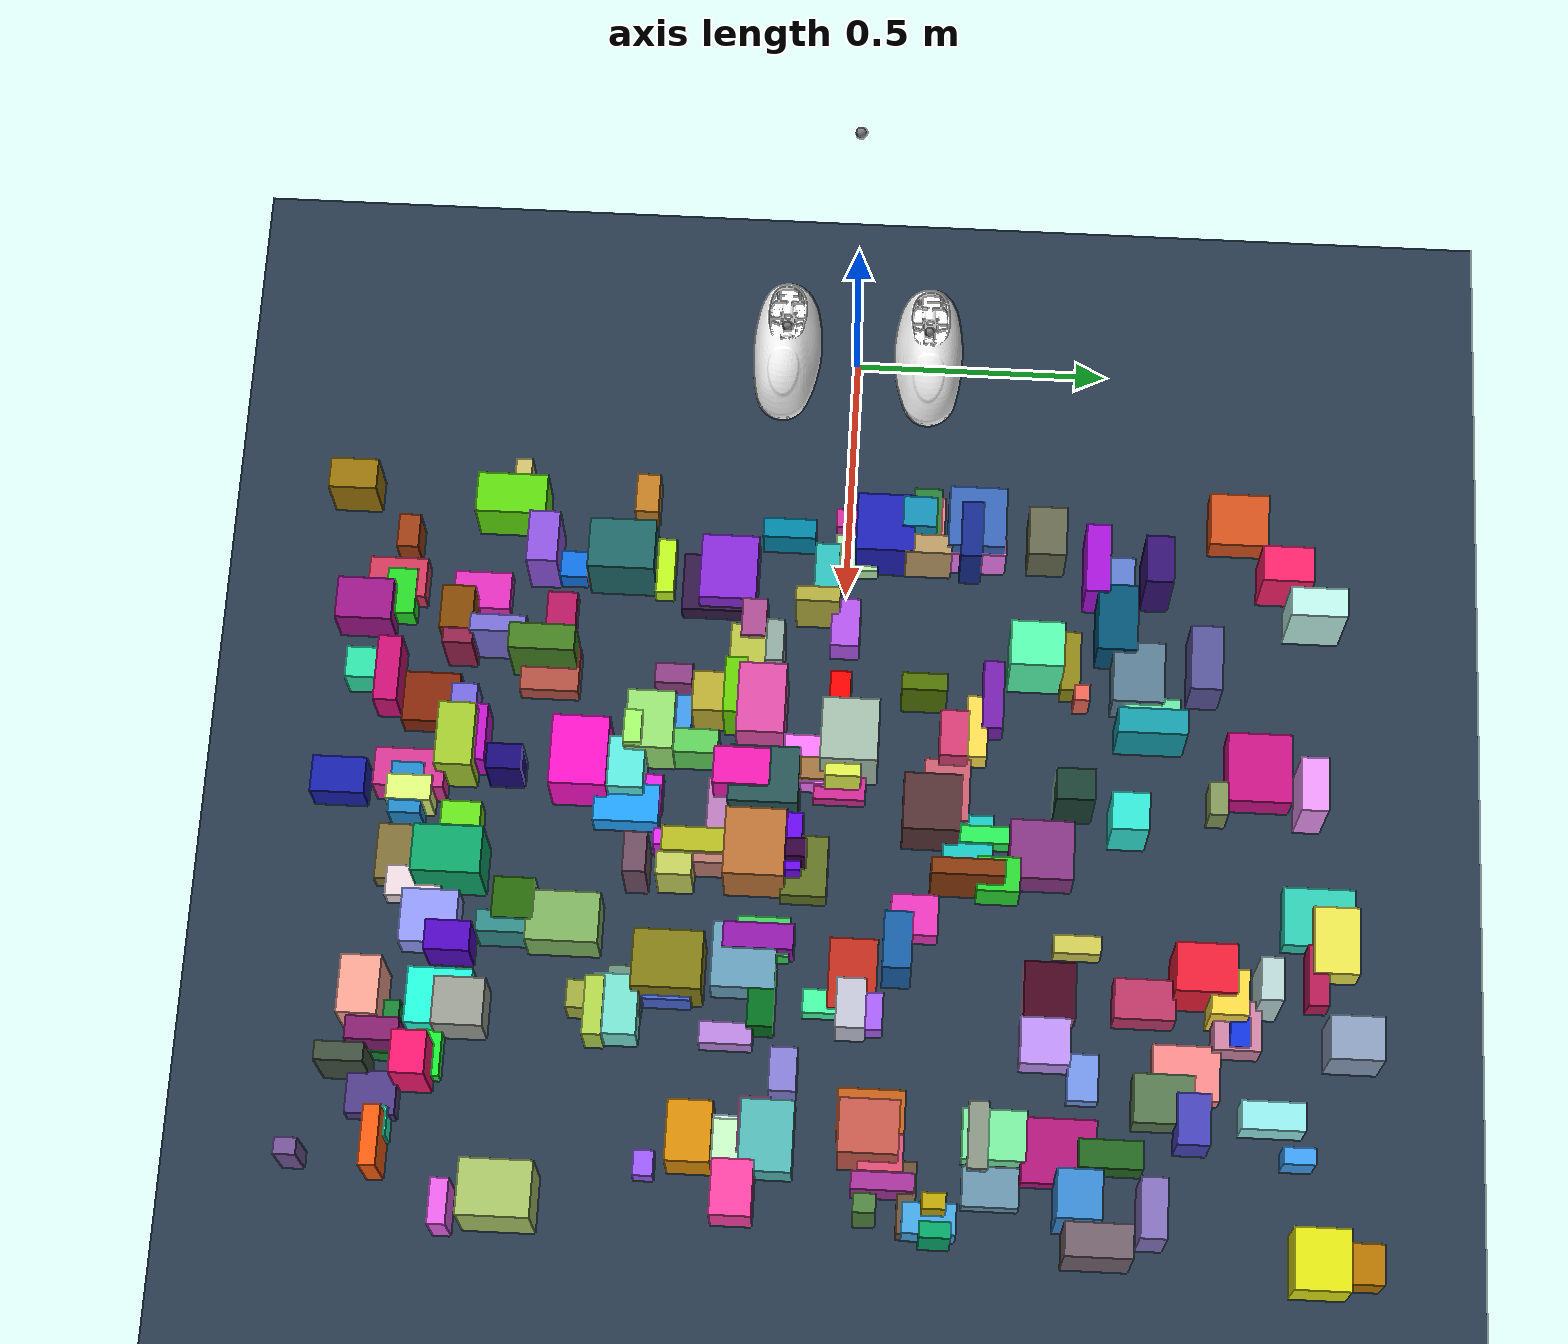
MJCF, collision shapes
<mujoco model="g1 scene">
  <include file="g1_29dof_rev_1_0.xml"/>

  <statistic center="1.0 0.7 1.0" extent="0.8"/>

  <visual>
    <headlight diffuse="0.6 0.6 0.6" ambient="0.1 0.1 0.1" specular="0.9 0.9 0.9"/>
    <rgba haze="0.15 0.25 0.35 1"/>
    <global azimuth="-140" elevation="-20"/>
  </visual>

  <asset>
    <texture type="skybox" builtin="flat" rgb1="0 0 0" rgb2="0 0 0" width="512" height="3072"/>
    <texture type="2d" name="groundplane" builtin="checker" mark="edge"
      rgb1="0.2 0.3 0.4" rgb2="0.1 0.2 0.3" markrgb="0.8 0.8 0.8" width="300" height="300"/>
    <material name="groundplane" texture="groundplane" texuniform="true"
      texrepeat="5 5" reflectance="0.2"/>
  </asset>

  <worldbody>
    <light pos="0 0 1.5" dir="0 0 -1" directional="true"/>
    <geom name="floor" size="0 0 0.05" type="plane" material="groundplane"/>
    <camera name="rgb_camera" pos="0 0 1.5" euler="0 0 0" fovy="60"/>
    <body name="cube" pos="0.75 0 0.05">
      <freejoint/>
      <geom type="box" size="0.05 0.02 0.06" rgba="1 0 0 1" mass="0.01" friction="3.0 2.0 0.003"/>
    </body>
    <!-- 200 auto-generated cubes  (single geom → collision == render geometry) -->
    <body name="cube_gen_000" pos="1.296 -0.297 0.066">
      <freejoint/>
      <geom name="cube_gen_000_geom" type="box" size="0.056 0.066 0.066" rgba="0.51 0.49 0.08 1" mass="0.033" friction="3.0 2.0 0.003"/>
    </body>
    <body name="cube_gen_001" pos="1.268 -0.156 0.041">
      <freejoint/>
      <geom name="cube_gen_001_geom" type="box" size="0.064 0.061 0.041" rgba="0.40 0.62 0.73 1" mass="0.027" friction="3.0 2.0 0.003"/>
    </body>
    <body name="cube_gen_002" pos="1.684 -0.975 0.062">
      <freejoint/>
      <geom name="cube_gen_002_geom" type="box" size="0.016 0.021 0.062" rgba="0.45 0.33 0.59 1" mass="0.028" friction="3.0 2.0 0.003"/>
    </body>
    <body name="cube_gen_003" pos="1.095 0.259 0.076">
      <freejoint/>
      <geom name="cube_gen_003_geom" type="box" size="0.016 0.070 0.076" rgba="0.53 0.22 0.05 1" mass="0.021" friction="3.0 2.0 0.003"/>
    </body>
    <body name="cube_gen_004" pos="1.741 0.092 0.071">
      <freejoint/>
      <geom name="cube_gen_004_geom" type="box" size="0.018 0.021 0.071" rgba="0.31 0.51 0.25 1" mass="0.014" friction="3.0 2.0 0.003"/>
    </body>
    <body name="cube_gen_005" pos="1.012 0.259 0.021">
      <freejoint/>
      <geom name="cube_gen_005_geom" type="box" size="0.054 0.048 0.021" rgba="0.10 0.78 0.76 1" mass="0.034" friction="3.0 2.0 0.003"/>
    </body>
    <body name="cube_gen_006" pos="0.455 0.608 0.079">
      <freejoint/>
      <geom name="cube_gen_006_geom" type="box" size="0.048 0.027 0.079" rgba="0.20 0.07 0.45 1" mass="0.023" friction="3.0 2.0 0.003"/>
    </body>
    <body name="cube_gen_007" pos="0.972 -0.815 0.049">
      <freejoint/>
      <geom name="cube_gen_007_geom" type="box" size="0.025 0.043 0.049" rgba="0.87 0.97 0.47 1" mass="0.016" friction="3.0 2.0 0.003"/>
    </body>
    <body name="cube_gen_008" pos="1.012 -0.714 0.037">
      <freejoint/>
      <geom name="cube_gen_008_geom" type="box" size="0.024 0.038 0.037" rgba="0.40 0.89 0.10 1" mass="0.036" friction="3.0 2.0 0.003"/>
    </body>
    <body name="cube_gen_009" pos="0.368 0.139 0.067">
      <freejoint/>
      <geom name="cube_gen_009_geom" type="box" size="0.031 0.033 0.067" rgba="0.08 0.56 0.71 1" mass="0.032" friction="3.0 2.0 0.003"/>
    </body>
    <body name="cube_gen_010" pos="1.357 0.050 0.052">
      <freejoint/>
      <geom name="cube_gen_010_geom" type="box" size="0.048 0.028 0.052" rgba="0.76 0.77 0.84 1" mass="0.039" friction="3.0 2.0 0.003"/>
    </body>
    <body name="cube_gen_011" pos="0.777 -0.149 0.077">
      <freejoint/>
      <geom name="cube_gen_011_geom" type="box" size="0.070 0.046 0.077" rgba="0.87 0.30 0.65 1" mass="0.029" friction="3.0 2.0 0.003"/>
    </body>
    <body name="cube_gen_012" pos="0.844 0.814 0.036">
      <freejoint/>
      <geom name="cube_gen_012_geom" type="box" size="0.069 0.062 0.036" rgba="0.79 0.07 0.52 1" mass="0.015" friction="3.0 2.0 0.003"/>
    </body>
    <body name="cube_gen_013" pos="1.461 -0.833 0.075">
      <freejoint/>
      <geom name="cube_gen_013_geom" type="box" size="0.022 0.050 0.075" rgba="0.52 0.11 0.43 1" mass="0.024" friction="3.0 2.0 0.003"/>
    </body>
    <body name="cube_gen_014" pos="1.415 -0.183 0.029">
      <freejoint/>
      <geom name="cube_gen_014_geom" type="box" size="0.021 0.050 0.029" rgba="0.73 0.52 0.87 1" mass="0.034" friction="3.0 2.0 0.003"/>
    </body>
    <body name="cube_gen_015" pos="1.751 0.212 0.039">
      <freejoint/>
      <geom name="cube_gen_015_geom" type="box" size="0.029 0.050 0.039" rgba="0.26 0.65 0.89 1" mass="0.027" friction="3.0 2.0 0.003"/>
    </body>
    <body name="cube_gen_016" pos="1.484 -0.071 0.040">
      <freejoint/>
      <geom name="cube_gen_016_geom" type="box" size="0.042 0.026 0.040" rgba="0.52 0.49 0.83 1" mass="0.014" friction="3.0 2.0 0.003"/>
    </body>
    <body name="cube_gen_017" pos="1.242 0.132 0.073">
      <freejoint/>
      <geom name="cube_gen_017_geom" type="box" size="0.055 0.027 0.073" rgba="0.09 0.37 0.65 1" mass="0.012" friction="3.0 2.0 0.003"/>
    </body>
    <body name="cube_gen_018" pos="0.392 0.073 0.065">
      <freejoint/>
      <geom name="cube_gen_018_geom" type="box" size="0.059 0.057 0.065" rgba="0.11 0.12 0.71 1" mass="0.032" friction="3.0 2.0 0.003"/>
    </body>
    <body name="cube_gen_019" pos="0.718 0.297 0.034">
      <freejoint/>
      <geom name="cube_gen_019_geom" type="box" size="0.069 0.020 0.034" rgba="0.46 0.12 0.68 1" mass="0.022" friction="3.0 2.0 0.003"/>
    </body>
    <body name="cube_gen_020" pos="0.917 -0.179 0.078">
      <freejoint/>
      <geom name="cube_gen_020_geom" type="box" size="0.037 0.054 0.078" rgba="0.94 0.10 0.69 1" mass="0.021" friction="3.0 2.0 0.003"/>
    </body>
    <body name="cube_gen_021" pos="1.601 0.094 0.078">
      <freejoint/>
      <geom name="cube_gen_021_geom" type="box" size="0.051 0.056 0.078" rgba="0.78 0.35 0.30 1" mass="0.040" friction="3.0 2.0 0.003"/>
    </body>
    <body name="cube_gen_022" pos="1.220 -0.757 0.040">
      <freejoint/>
      <geom name="cube_gen_022_geom" type="box" size="0.052 0.054 0.040" rgba="0.57 0.60 0.98 1" mass="0.028" friction="3.0 2.0 0.003"/>
    </body>
    <body name="cube_gen_023" pos="1.668 -0.321 0.026">
      <freejoint/>
      <geom name="cube_gen_023_geom" type="box" size="0.024 0.019 0.026" rgba="0.60 0.35 0.98 1" mass="0.025" friction="3.0 2.0 0.003"/>
    </body>
    <body name="cube_gen_024" pos="0.731 0.605 0.039">
      <freejoint/>
      <geom name="cube_gen_024_geom" type="box" size="0.016 0.054 0.039" rgba="0.41 0.89 0.65 1" mass="0.037" friction="3.0 2.0 0.003"/>
    </body>
    <body name="cube_gen_025" pos="1.210 0.473 0.028">
      <freejoint/>
      <geom name="cube_gen_025_geom" type="box" size="0.018 0.045 0.028" rgba="0.80 0.79 0.32 1" mass="0.038" friction="3.0 2.0 0.003"/>
    </body>
    <body name="cube_gen_026" pos="1.748 -0.582 0.076">
      <freejoint/>
      <geom name="cube_gen_026_geom" type="box" size="0.053 0.068 0.076" rgba="0.66 0.77 0.40 1" mass="0.028" friction="3.0 2.0 0.003"/>
    </body>
    <body name="cube_gen_027" pos="0.853 -0.296 0.051">
      <freejoint/>
      <geom name="cube_gen_027_geom" type="box" size="0.024 0.067 0.051" rgba="0.37 0.81 0.35 1" mass="0.032" friction="3.0 2.0 0.003"/>
    </body>
    <body name="cube_gen_028" pos="1.721 0.621 0.064">
      <freejoint/>
      <geom name="cube_gen_028_geom" type="box" size="0.057 0.025 0.064" rgba="0.51 0.44 0.74 1" mass="0.023" friction="3.0 2.0 0.003"/>
    </body>
    <body name="cube_gen_029" pos="0.655 -0.130 0.073">
      <freejoint/>
      <geom name="cube_gen_029_geom" type="box" size="0.042 0.017 0.073" rgba="0.57 0.66 0.63 1" mass="0.013" friction="3.0 2.0 0.003"/>
    </body>
    <body name="cube_gen_030" pos="1.625 -0.163 0.032">
      <freejoint/>
      <geom name="cube_gen_030_geom" type="box" size="0.045 0.068 0.032" rgba="0.78 0.97 0.76 1" mass="0.028" friction="3.0 2.0 0.003"/>
    </body>
    <body name="cube_gen_031" pos="1.146 -0.795 0.027">
      <freejoint/>
      <geom name="cube_gen_031_geom" type="box" size="0.030 0.053 0.027" rgba="0.93 0.85 0.88 1" mass="0.014" friction="3.0 2.0 0.003"/>
    </body>
    <body name="cube_gen_032" pos="1.081 -0.052 0.030">
      <freejoint/>
      <geom name="cube_gen_032_geom" type="box" size="0.060 0.044 0.030" rgba="0.38 0.45 0.14 1" mass="0.036" friction="3.0 2.0 0.003"/>
    </body>
    <body name="cube_gen_033" pos="1.063 -0.146 0.073">
      <freejoint/>
      <geom name="cube_gen_033_geom" type="box" size="0.066 0.058 0.073" rgba="0.74 0.45 0.21 1" mass="0.038" friction="3.0 2.0 0.003"/>
    </body>
    <body name="cube_gen_034" pos="0.971 -0.821 0.046">
      <freejoint/>
      <geom name="cube_gen_034_geom" type="box" size="0.051 0.031 0.046" rgba="0.13 0.54 0.80 1" mass="0.023" friction="3.0 2.0 0.003"/>
    </body>
    <body name="cube_gen_035" pos="0.480 -0.547 0.027">
      <freejoint/>
      <geom name="cube_gen_035_geom" type="box" size="0.027 0.037 0.027" rgba="0.06 0.44 0.89 1" mass="0.025" friction="3.0 2.0 0.003"/>
    </body>
    <body name="cube_gen_036" pos="1.216 -0.501 0.053">
      <freejoint/>
      <geom name="cube_gen_036_geom" type="box" size="0.049 0.069 0.053" rgba="0.49 0.70 0.37 1" mass="0.032" friction="3.0 2.0 0.003"/>
    </body>
    <body name="cube_gen_037" pos="0.895 0.007 0.020">
      <freejoint/>
      <geom name="cube_gen_037_geom" type="box" size="0.043 0.050 0.020" rgba="0.80 0.16 0.57 1" mass="0.014" friction="3.0 2.0 0.003"/>
    </body>
    <body name="cube_gen_038" pos="0.441 0.491 0.058">
      <freejoint/>
      <geom name="cube_gen_038_geom" type="box" size="0.070 0.024 0.058" rgba="0.65 0.07 0.84 1" mass="0.024" friction="3.0 2.0 0.003"/>
    </body>
    <body name="cube_gen_039" pos="0.902 0.013 0.061">
      <freejoint/>
      <geom name="cube_gen_039_geom" type="box" size="0.015 0.034 0.061" rgba="0.87 0.94 0.30 1" mass="0.015" friction="3.0 2.0 0.003"/>
    </body>
    <body name="cube_gen_040" pos="0.998 0.297 0.025">
      <freejoint/>
      <geom name="cube_gen_040_geom" type="box" size="0.017 0.054 0.025" rgba="0.16 0.93 0.34 1" mass="0.019" friction="3.0 2.0 0.003"/>
    </body>
    <body name="cube_gen_041" pos="0.330 -0.401 0.038">
      <freejoint/>
      <geom name="cube_gen_041_geom" type="box" size="0.040 0.023 0.038" rgba="0.76 0.49 0.14 1" mass="0.035" friction="3.0 2.0 0.003"/>
    </body>
    <body name="cube_gen_042" pos="1.385 -0.431 0.053">
      <freejoint/>
      <geom name="cube_gen_042_geom" type="box" size="0.057 0.018 0.053" rgba="0.69 0.83 0.29 1" mass="0.026" friction="3.0 2.0 0.003"/>
    </body>
    <body name="cube_gen_043" pos="1.049 -0.093 0.056">
      <freejoint/>
      <geom name="cube_gen_043_geom" type="box" size="0.057 0.035 0.056" rgba="0.41 0.03 0.93 1" mass="0.019" friction="3.0 2.0 0.003"/>
    </body>
    <body name="cube_gen_044" pos="1.447 0.683 0.025">
      <freejoint/>
      <geom name="cube_gen_044_geom" type="box" size="0.052 0.063 0.025" rgba="0.97 0.54 0.54 1" mass="0.029" friction="3.0 2.0 0.003"/>
    </body>
    <body name="cube_gen_045" pos="1.731 0.219 0.071">
      <freejoint/>
      <geom name="cube_gen_045_geom" type="box" size="0.015 0.022 0.071" rgba="0.74 0.65 0.02 1" mass="0.025" friction="3.0 2.0 0.003"/>
    </body>
    <body name="cube_gen_046" pos="0.893 -0.492 0.067">
      <freejoint/>
      <geom name="cube_gen_046_geom" type="box" size="0.069 0.055 0.067" rgba="0.98 0.07 0.78 1" mass="0.016" friction="3.0 2.0 0.003"/>
    </body>
    <body name="cube_gen_047" pos="0.639 0.705 0.058">
      <freejoint/>
      <geom name="cube_gen_047_geom" type="box" size="0.065 0.031 0.058" rgba="0.34 0.33 0.60 1" mass="0.011" friction="3.0 2.0 0.003"/>
    </body>
    <body name="cube_gen_048" pos="1.796 0.997 0.040">
      <freejoint/>
      <geom name="cube_gen_048_geom" type="box" size="0.038 0.051 0.040" rgba="0.71 0.46 0.00 1" mass="0.026" friction="3.0 2.0 0.003"/>
    </body>
    <body name="cube_gen_049" pos="1.505 0.640 0.038">
      <freejoint/>
      <geom name="cube_gen_049_geom" type="box" size="0.047 0.057 0.038" rgba="0.34 0.47 0.31 1" mass="0.033" friction="3.0 2.0 0.003"/>
    </body>
    <body name="cube_gen_050" pos="0.641 0.445 0.034">
      <freejoint/>
      <geom name="cube_gen_050_geom" type="box" size="0.060 0.019 0.034" rgba="0.55 0.53 0.09 1" mass="0.035" friction="3.0 2.0 0.003"/>
    </body>
    <body name="cube_gen_051" pos="1.089 0.318 0.047">
      <freejoint/>
      <geom name="cube_gen_051_geom" type="box" size="0.034 0.041 0.047" rgba="0.16 0.85 0.19 1" mass="0.024" friction="3.0 2.0 0.003"/>
    </body>
    <body name="cube_gen_052" pos="1.134 0.931 0.028">
      <freejoint/>
      <geom name="cube_gen_052_geom" type="box" size="0.057 0.068 0.028" rgba="0.18 0.80 0.70 1" mass="0.017" friction="3.0 2.0 0.003"/>
    </body>
    <body name="cube_gen_053" pos="0.381 0.143 0.037">
      <freejoint/>
      <geom name="cube_gen_053_geom" type="box" size="0.069 0.046 0.037" rgba="0.96 0.46 0.50 1" mass="0.028" friction="3.0 2.0 0.003"/>
    </body>
    <body name="cube_gen_054" pos="0.864 -0.054 0.028">
      <freejoint/>
      <geom name="cube_gen_054_geom" type="box" size="0.049 0.055 0.028" rgba="0.97 0.47 0.98 1" mass="0.037" friction="3.0 2.0 0.003"/>
    </body>
    <body name="cube_gen_055" pos="0.590 -0.556 0.023">
      <freejoint/>
      <geom name="cube_gen_055_geom" type="box" size="0.053 0.029 0.023" rgba="0.71 0.09 0.38 1" mass="0.017" friction="3.0 2.0 0.003"/>
    </body>
    <body name="cube_gen_056" pos="1.589 -0.120 0.033">
      <freejoint/>
      <geom name="cube_gen_056_geom" type="box" size="0.053 0.029 0.033" rgba="0.80 0.35 0.59 1" mass="0.035" friction="3.0 2.0 0.003"/>
    </body>
    <body name="cube_gen_057" pos="0.971 -0.400 0.031">
      <freejoint/>
      <geom name="cube_gen_057_geom" type="box" size="0.038 0.063 0.031" rgba="0.13 0.63 0.99 1" mass="0.037" friction="3.0 2.0 0.003"/>
    </body>
    <body name="cube_gen_058" pos="1.338 -0.379 0.030">
      <freejoint/>
      <geom name="cube_gen_058_geom" type="box" size="0.044 0.032 0.030" rgba="0.40 0.55 0.48 1" mass="0.035" friction="3.0 2.0 0.003"/>
    </body>
    <body name="cube_gen_059" pos="0.872 -0.731 0.068">
      <freejoint/>
      <geom name="cube_gen_059_geom" type="box" size="0.063 0.036 0.068" rgba="0.64 0.79 0.18 1" mass="0.039" friction="3.0 2.0 0.003"/>
    </body>
    <body name="cube_gen_060" pos="1.601 0.892 0.039">
      <freejoint/>
      <geom name="cube_gen_060_geom" type="box" size="0.016 0.030 0.039" rgba="0.24 0.62 0.95 1" mass="0.023" friction="3.0 2.0 0.003"/>
    </body>
    <body name="cube_gen_061" pos="1.183 0.962 0.038">
      <freejoint/>
      <geom name="cube_gen_061_geom" type="box" size="0.065 0.044 0.038" rgba="0.92 0.90 0.31 1" mass="0.034" friction="3.0 2.0 0.003"/>
    </body>
    <body name="cube_gen_062" pos="0.747 -0.202 0.069">
      <freejoint/>
      <geom name="cube_gen_062_geom" type="box" size="0.056 0.021 0.069" rgba="0.40 0.82 0.01 1" mass="0.017" friction="3.0 2.0 0.003"/>
    </body>
    <body name="cube_gen_063" pos="1.379 -0.723 0.047">
      <freejoint/>
      <geom name="cube_gen_063_geom" type="box" size="0.054 0.061 0.047" rgba="0.14 0.99 0.85 1" mass="0.022" friction="3.0 2.0 0.003"/>
    </body>
    <body name="cube_gen_064" pos="1.094 -0.371 0.072">
      <freejoint/>
      <geom name="cube_gen_064_geom" type="box" size="0.039 0.022 0.072" rgba="0.43 0.30 0.38 1" mass="0.019" friction="3.0 2.0 0.003"/>
    </body>
    <body name="cube_gen_065" pos="0.755 -0.223 0.058">
      <freejoint/>
      <geom name="cube_gen_065_geom" type="box" size="0.040 0.061 0.058" rgba="0.73 0.67 0.19 1" mass="0.039" friction="3.0 2.0 0.003"/>
    </body>
    <body name="cube_gen_066" pos="0.393 -0.116 0.040">
      <freejoint/>
      <geom name="cube_gen_066_geom" type="box" size="0.020 0.052 0.040" rgba="0.00 0.52 0.65 1" mass="0.031" friction="3.0 2.0 0.003"/>
    </body>
    <body name="cube_gen_067" pos="0.529 0.917 0.078">
      <freejoint/>
      <geom name="cube_gen_067_geom" type="box" size="0.029 0.055 0.078" rgba="0.74 0.95 0.91 1" mass="0.015" friction="3.0 2.0 0.003"/>
    </body>
    <body name="cube_gen_068" pos="0.929 -0.136 0.074">
      <freejoint/>
      <geom name="cube_gen_068_geom" type="box" size="0.056 0.067 0.074" rgba="0.15 0.33 0.33 1" mass="0.028" friction="3.0 2.0 0.003"/>
    </body>
    <body name="cube_gen_069" pos="1.788 0.521 0.071">
      <freejoint/>
      <geom name="cube_gen_069_geom" type="box" size="0.032 0.063 0.071" rgba="0.45 0.38 0.42 1" mass="0.022" friction="3.0 2.0 0.003"/>
    </body>
    <body name="cube_gen_070" pos="0.979 -0.183 0.035">
      <freejoint/>
      <geom name="cube_gen_070_geom" type="box" size="0.062 0.061 0.035" rgba="0.73 0.48 0.73 1" mass="0.038" friction="3.0 2.0 0.003"/>
    </body>
    <body name="cube_gen_071" pos="1.088 -0.815 0.026">
      <freejoint/>
      <geom name="cube_gen_071_geom" type="box" size="0.055 0.057 0.026" rgba="0.50 0.44 0.22 1" mass="0.026" friction="3.0 2.0 0.003"/>
    </body>
    <body name="cube_gen_072" pos="1.318 -0.331 0.032">
      <freejoint/>
      <geom name="cube_gen_072_geom" type="box" size="0.031 0.038 0.032" rgba="0.94 0.94 0.88 1" mass="0.028" friction="3.0 2.0 0.003"/>
    </body>
    <body name="cube_gen_073" pos="0.334 -0.980 0.059">
      <freejoint/>
      <geom name="cube_gen_073_geom" type="box" size="0.031 0.047 0.059" rgba="0.60 0.45 0.04 1" mass="0.015" friction="3.0 2.0 0.003"/>
    </body>
    <body name="cube_gen_074" pos="1.268 0.710 0.074">
      <freejoint/>
      <geom name="cube_gen_074_geom" type="box" size="0.047 0.058 0.074" rgba="0.93 0.11 0.21 1" mass="0.019" friction="3.0 2.0 0.003"/>
    </body>
    <body name="cube_gen_075" pos="0.702 -0.568 0.026">
      <freejoint/>
      <geom name="cube_gen_075_geom" type="box" size="0.044 0.057 0.026" rgba="0.70 0.31 0.26 1" mass="0.034" friction="3.0 2.0 0.003"/>
    </body>
    <body name="cube_gen_076" pos="0.780 0.602 0.066">
      <freejoint/>
      <geom name="cube_gen_076_geom" type="box" size="0.025 0.067 0.066" rgba="0.08 0.62 0.67 1" mass="0.038" friction="3.0 2.0 0.003"/>
    </body>
    <body name="cube_gen_077" pos="0.440 -0.864 0.046">
      <freejoint/>
      <geom name="cube_gen_077_geom" type="box" size="0.034 0.021 0.046" rgba="0.62 0.24 0.07 1" mass="0.019" friction="3.0 2.0 0.003"/>
    </body>
    <body name="cube_gen_078" pos="1.435 -0.827 0.032">
      <freejoint/>
      <geom name="cube_gen_078_geom" type="box" size="0.051 0.030 0.032" rgba="0.10 0.51 0.20 1" mass="0.014" friction="3.0 2.0 0.003"/>
    </body>
    <body name="cube_gen_079" pos="1.182 -0.777 0.025">
      <freejoint/>
      <geom name="cube_gen_079_geom" type="box" size="0.037 0.030 0.025" rgba="0.42 0.40 0.23 1" mass="0.011" friction="3.0 2.0 0.003"/>
    </body>
    <body name="cube_gen_080" pos="1.042 -0.280 0.040">
      <freejoint/>
      <geom name="cube_gen_080_geom" type="box" size="0.016 0.063 0.040" rgba="0.88 0.17 0.95 1" mass="0.013" friction="3.0 2.0 0.003"/>
    </body>
    <body name="cube_gen_081" pos="1.707 0.483 0.077">
      <freejoint/>
      <geom name="cube_gen_081_geom" type="box" size="0.046 0.042 0.077" rgba="0.22 0.54 0.82 1" mass="0.024" friction="3.0 2.0 0.003"/>
    </body>
    <body name="cube_gen_082" pos="0.325 0.771 0.032">
      <freejoint/>
      <geom name="cube_gen_082_geom" type="box" size="0.054 0.058 0.032" rgba="0.83 0.32 0.11 1" mass="0.026" friction="3.0 2.0 0.003"/>
    </body>
    <body name="cube_gen_083" pos="1.222 -0.122 0.027">
      <freejoint/>
      <geom name="cube_gen_083_geom" type="box" size="0.038 0.050 0.027" rgba="0.24 0.81 0.36 1" mass="0.039" friction="3.0 2.0 0.003"/>
    </body>
    <body name="cube_gen_084" pos="0.413 0.018 0.021">
      <freejoint/>
      <geom name="cube_gen_084_geom" type="box" size="0.048 0.042 0.021" rgba="0.70 0.93 0.67 1" mass="0.015" friction="3.0 2.0 0.003"/>
    </body>
    <body name="cube_gen_085" pos="0.388 0.391 0.057">
      <freejoint/>
      <geom name="cube_gen_085_geom" type="box" size="0.050 0.037 0.057" rgba="0.40 0.41 0.31 1" mass="0.013" friction="3.0 2.0 0.003"/>
    </body>
    <body name="cube_gen_086" pos="1.507 -0.890 0.074">
      <freejoint/>
      <geom name="cube_gen_086_geom" type="box" size="0.018 0.046 0.074" rgba="0.25 0.31 0.25 1" mass="0.016" friction="3.0 2.0 0.003"/>
    </body>
    <body name="cube_gen_087" pos="0.904 -0.418 0.054">
      <freejoint/>
      <geom name="cube_gen_087_geom" type="box" size="0.051 0.050 0.054" rgba="0.36 0.91 0.87 1" mass="0.029" friction="3.0 2.0 0.003"/>
    </body>
    <body name="cube_gen_088" pos="0.648 -0.666 0.075">
      <freejoint/>
      <geom name="cube_gen_088_geom" type="box" size="0.017 0.054 0.075" rgba="0.47 0.43 0.84 1" mass="0.025" friction="3.0 2.0 0.003"/>
    </body>
    <body name="cube_gen_089" pos="0.376 0.252 0.070">
      <freejoint/>
      <geom name="cube_gen_089_geom" type="box" size="0.062 0.056 0.070" rgba="0.22 0.40 0.72 1" mass="0.030" friction="3.0 2.0 0.003"/>
    </body>
    <body name="cube_gen_090" pos="0.462 0.525 0.047">
      <freejoint/>
      <geom name="cube_gen_090_geom" type="box" size="0.032 0.039 0.047" rgba="0.37 0.49 0.81 1" mass="0.036" friction="3.0 2.0 0.003"/>
    </body>
    <body name="cube_gen_091" pos="0.896 0.911 0.071">
      <freejoint/>
      <geom name="cube_gen_091_geom" type="box" size="0.053 0.026 0.071" rgba="0.93 0.59 0.97 1" mass="0.014" friction="3.0 2.0 0.003"/>
    </body>
    <body name="cube_gen_092" pos="1.457 -0.739 0.023">
      <freejoint/>
      <geom name="cube_gen_092_geom" type="box" size="0.064 0.024 0.023" rgba="0.11 0.93 0.20 1" mass="0.023" friction="3.0 2.0 0.003"/>
    </body>
    <body name="cube_gen_093" pos="0.653 -0.171 0.047">
      <freejoint/>
      <geom name="cube_gen_093_geom" type="box" size="0.048 0.047 0.047" rgba="0.73 0.76 0.27 1" mass="0.033" friction="3.0 2.0 0.003"/>
    </body>
    <body name="cube_gen_094" pos="0.844 -0.392 0.073">
      <freejoint/>
      <geom name="cube_gen_094_geom" type="box" size="0.033 0.017 0.073" rgba="0.63 0.98 0.42 1" mass="0.028" friction="3.0 2.0 0.003"/>
    </body>
    <body name="cube_gen_095" pos="1.052 -0.262 0.053">
      <freejoint/>
      <geom name="cube_gen_095_geom" type="box" size="0.024 0.063 0.053" rgba="0.71 0.73 0.13 1" mass="0.027" friction="3.0 2.0 0.003"/>
    </body>
    <body name="cube_gen_096" pos="0.590 -0.936 0.051">
      <freejoint/>
      <geom name="cube_gen_096_geom" type="box" size="0.042 0.055 0.051" rgba="0.61 0.08 0.54 1" mass="0.038" friction="3.0 2.0 0.003"/>
    </body>
    <body name="cube_gen_097" pos="0.433 0.159 0.064">
      <freejoint/>
      <geom name="cube_gen_097_geom" type="box" size="0.019 0.045 0.064" rgba="0.73 0.60 0.39 1" mass="0.037" friction="3.0 2.0 0.003"/>
    </body>
    <body name="cube_gen_098" pos="1.307 0.756 0.063">
      <freejoint/>
      <geom name="cube_gen_098_geom" type="box" size="0.044 0.036 0.063" rgba="0.99 0.85 0.26 1" mass="0.037" friction="3.0 2.0 0.003"/>
    </body>
    <body name="cube_gen_099" pos="1.795 0.933 0.051">
      <freejoint/>
      <geom name="cube_gen_099_geom" type="box" size="0.058 0.053 0.051" rgba="0.88 0.90 0.07 1" mass="0.014" friction="3.0 2.0 0.003"/>
    </body>
    <body name="cube_gen_100" pos="1.680 0.324 0.021">
      <freejoint/>
      <geom name="cube_gen_100_geom" type="box" size="0.038 0.053 0.021" rgba="0.41 0.58 0.67 1" mass="0.018" friction="3.0 2.0 0.003"/>
    </body>
    <body name="cube_gen_101" pos="1.558 0.097 0.046">
      <freejoint/>
      <geom name="cube_gen_101_geom" type="box" size="0.041 0.063 0.046" rgba="0.78 0.37 0.09 1" mass="0.023" friction="3.0 2.0 0.003"/>
    </body>
    <body name="cube_gen_102" pos="1.503 -0.762 0.077">
      <freejoint/>
      <geom name="cube_gen_102_geom" type="box" size="0.041 0.033 0.077" rgba="0.97 0.09 0.44 1" mass="0.025" friction="3.0 2.0 0.003"/>
    </body>
    <body name="cube_gen_103" pos="0.784 0.268 0.032">
      <freejoint/>
      <geom name="cube_gen_103_geom" type="box" size="0.062 0.020 0.032" rgba="1.00 0.86 0.31 1" mass="0.022" friction="3.0 2.0 0.003"/>
    </body>
    <body name="cube_gen_104" pos="0.424 0.242 0.050">
      <freejoint/>
      <geom name="cube_gen_104_geom" type="box" size="0.016 0.069 0.050" rgba="0.95 0.49 0.95 1" mass="0.013" friction="3.0 2.0 0.003"/>
    </body>
    <body name="cube_gen_105" pos="1.546 0.694 0.050">
      <freejoint/>
      <geom name="cube_gen_105_geom" type="box" size="0.049 0.031 0.050" rgba="0.27 0.26 0.73 1" mass="0.034" friction="3.0 2.0 0.003"/>
    </body>
    <body name="cube_gen_106" pos="1.584 0.328 0.028">
      <freejoint/>
      <geom name="cube_gen_106_geom" type="box" size="0.048 0.060 0.028" rgba="0.47 0.92 0.62 1" mass="0.026" friction="3.0 2.0 0.003"/>
    </body>
    <body name="cube_gen_107" pos="0.817 0.223 0.057">
      <freejoint/>
      <geom name="cube_gen_107_geom" type="box" size="0.046 0.027 0.057" rgba="0.83 0.23 0.45 1" mass="0.012" friction="3.0 2.0 0.003"/>
    </body>
    <body name="cube_gen_108" pos="0.929 -0.819 0.044">
      <freejoint/>
      <geom name="cube_gen_108_geom" type="box" size="0.038 0.068 0.044" rgba="0.84 0.21 0.58 1" mass="0.035" friction="3.0 2.0 0.003"/>
    </body>
    <body name="cube_gen_109" pos="0.667 0.576 0.047">
      <freejoint/>
      <geom name="cube_gen_109_geom" type="box" size="0.061 0.050 0.047" rgba="0.35 0.49 0.58 1" mass="0.020" friction="3.0 2.0 0.003"/>
    </body>
    <body name="cube_gen_110" pos="0.367 -0.000 0.040">
      <freejoint/>
      <geom name="cube_gen_110_geom" type="box" size="0.019 0.025 0.040" rgba="0.81 0.19 0.61 1" mass="0.019" friction="3.0 2.0 0.003"/>
    </body>
    <body name="cube_gen_111" pos="1.378 -0.391 0.047">
      <freejoint/>
      <geom name="cube_gen_111_geom" type="box" size="0.058 0.042 0.047" rgba="0.46 0.88 0.81 1" mass="0.023" friction="3.0 2.0 0.003"/>
    </body>
    <body name="cube_gen_112" pos="0.886 -0.049 0.035">
      <freejoint/>
      <geom name="cube_gen_112_geom" type="box" size="0.022 0.040 0.035" rgba="0.63 0.45 0.24 1" mass="0.021" friction="3.0 2.0 0.003"/>
    </body>
    <body name="cube_gen_113" pos="0.359 0.154 0.037">
      <freejoint/>
      <geom name="cube_gen_113_geom" type="box" size="0.066 0.028 0.037" rgba="0.16 0.49 0.22 1" mass="0.029" friction="3.0 2.0 0.003"/>
    </body>
    <body name="cube_gen_114" pos="0.595 -0.174 0.054">
      <freejoint/>
      <geom name="cube_gen_114_geom" type="box" size="0.038 0.024 0.054" rgba="0.67 0.30 0.58 1" mass="0.023" friction="3.0 2.0 0.003"/>
    </body>
    <body name="cube_gen_115" pos="0.673 -0.579 0.077">
      <freejoint/>
      <geom name="cube_gen_115_geom" type="box" size="0.026 0.064 0.077" rgba="0.27 0.50 0.13 1" mass="0.028" friction="3.0 2.0 0.003"/>
    </body>
    <body name="cube_gen_116" pos="0.942 -0.377 0.022">
      <freejoint/>
      <geom name="cube_gen_116_geom" type="box" size="0.036 0.043 0.022" rgba="0.90 0.14 0.89 1" mass="0.014" friction="3.0 2.0 0.003"/>
    </body>
    <body name="cube_gen_117" pos="0.709 0.468 0.039">
      <freejoint/>
      <geom name="cube_gen_117_geom" type="box" size="0.016 0.015 0.039" rgba="0.93 0.40 0.33 1" mass="0.017" friction="3.0 2.0 0.003"/>
    </body>
    <body name="cube_gen_118" pos="1.339 -0.119 0.041">
      <freejoint/>
      <geom name="cube_gen_118_geom" type="box" size="0.066 0.025 0.041" rgba="0.01 0.43 0.12 1" mass="0.036" friction="3.0 2.0 0.003"/>
    </body>
    <body name="cube_gen_119" pos="1.527 0.844 0.038">
      <freejoint/>
      <geom name="cube_gen_119_geom" type="box" size="0.027 0.060 0.038" rgba="0.58 0.92 0.92 1" mass="0.023" friction="3.0 2.0 0.003"/>
    </body>
    <body name="cube_gen_120" pos="1.286 0.831 0.078">
      <freejoint/>
      <geom name="cube_gen_120_geom" type="box" size="0.041 0.022 0.078" rgba="0.72 0.83 0.83 1" mass="0.024" friction="3.0 2.0 0.003"/>
    </body>
    <body name="cube_gen_121" pos="1.464 0.490 0.021">
      <freejoint/>
      <geom name="cube_gen_121_geom" type="box" size="0.045 0.029 0.021" rgba="0.45 0.58 0.91 1" mass="0.036" friction="3.0 2.0 0.003"/>
    </body>
    <body name="cube_gen_122" pos="0.467 -0.439 0.071">
      <freejoint/>
      <geom name="cube_gen_122_geom" type="box" size="0.051 0.065 0.071" rgba="0.12 0.40 0.40 1" mass="0.022" friction="3.0 2.0 0.003"/>
    </body>
    <body name="cube_gen_123" pos="1.607 0.449 0.023">
      <freejoint/>
      <geom name="cube_gen_123_geom" type="box" size="0.062 0.070 0.023" rgba="0.69 0.08 0.47 1" mass="0.021" friction="3.0 2.0 0.003"/>
    </body>
    <body name="cube_gen_124" pos="0.913 0.214 0.028">
      <freejoint/>
      <geom name="cube_gen_124_geom" type="box" size="0.062 0.044 0.028" rgba="0.79 0.36 0.43 1" mass="0.027" friction="3.0 2.0 0.003"/>
    </body>
    <body name="cube_gen_125" pos="0.791 -0.322 0.043">
      <freejoint/>
      <geom name="cube_gen_125_geom" type="box" size="0.045 0.038 0.043" rgba="0.24 0.59 0.92 1" mass="0.017" friction="3.0 2.0 0.003"/>
    </body>
    <body name="cube_gen_126" pos="0.830 0.023 0.074">
      <freejoint/>
      <geom name="cube_gen_126_geom" type="box" size="0.062 0.055 0.074" rgba="0.64 0.74 0.67 1" mass="0.028" friction="3.0 2.0 0.003"/>
    </body>
    <body name="cube_gen_127" pos="1.770 -0.687 0.057">
      <freejoint/>
      <geom name="cube_gen_127_geom" type="box" size="0.043 0.017 0.057" rgba="0.92 0.38 0.92 1" mass="0.015" friction="3.0 2.0 0.003"/>
    </body>
    <body name="cube_gen_128" pos="0.503 -0.257 0.024">
      <freejoint/>
      <geom name="cube_gen_128_geom" type="box" size="0.058 0.064 0.024" rgba="0.19 0.09 0.27 1" mass="0.034" friction="3.0 2.0 0.003"/>
    </body>
    <body name="cube_gen_129" pos="1.560 -0.837 0.027">
      <freejoint/>
      <geom name="cube_gen_129_geom" type="box" size="0.041 0.047 0.027" rgba="0.31 0.23 0.54 1" mass="0.018" friction="3.0 2.0 0.003"/>
    </body>
    <body name="cube_gen_130" pos="1.316 0.601 0.038">
      <freejoint/>
      <geom name="cube_gen_130_geom" type="box" size="0.039 0.058 0.038" rgba="0.74 0.21 0.40 1" mass="0.019" friction="3.0 2.0 0.003"/>
    </body>
    <body name="cube_gen_131" pos="0.907 -0.636 0.058">
      <freejoint/>
      <geom name="cube_gen_131_geom" type="box" size="0.025 0.034 0.058" rgba="0.10 0.03 0.47 1" mass="0.016" friction="3.0 2.0 0.003"/>
    </body>
    <body name="cube_gen_132" pos="0.920 0.457 0.074">
      <freejoint/>
      <geom name="cube_gen_132_geom" type="box" size="0.031 0.037 0.074" rgba="0.10 0.25 0.20 1" mass="0.010" friction="3.0 2.0 0.003"/>
    </body>
    <body name="cube_gen_133" pos="1.266 -0.714 0.057">
      <freejoint/>
      <geom name="cube_gen_133_geom" type="box" size="0.029 0.043 0.057" rgba="0.32 0.02 0.76 1" mass="0.025" friction="3.0 2.0 0.003"/>
    </body>
    <body name="cube_gen_134" pos="1.342 -0.002 0.023">
      <freejoint/>
      <geom name="cube_gen_134_geom" type="box" size="0.023 0.040 0.023" rgba="0.27 0.98 0.64 1" mass="0.016" friction="3.0 2.0 0.003"/>
    </body>
    <body name="cube_gen_135" pos="0.556 -0.872 0.031">
      <freejoint/>
      <geom name="cube_gen_135_geom" type="box" size="0.047 0.029 0.031" rgba="0.15 0.85 0.15 1" mass="0.019" friction="3.0 2.0 0.003"/>
    </body>
    <body name="cube_gen_136" pos="0.472 -0.357 0.024">
      <freejoint/>
      <geom name="cube_gen_136_geom" type="box" size="0.056 0.018 0.024" rgba="0.74 0.96 0.12 1" mass="0.026" friction="3.0 2.0 0.003"/>
    </body>
    <body name="cube_gen_137" pos="0.732 -0.878 0.050">
      <freejoint/>
      <geom name="cube_gen_137_geom" type="box" size="0.066 0.023 0.050" rgba="0.80 0.06 0.46 1" mass="0.034" friction="3.0 2.0 0.003"/>
    </body>
    <body name="cube_gen_138" pos="1.607 -0.142 0.020">
      <freejoint/>
      <geom name="cube_gen_138_geom" type="box" size="0.039 0.056 0.020" rgba="0.79 0.94 0.95 1" mass="0.027" friction="3.0 2.0 0.003"/>
    </body>
    <body name="cube_gen_139" pos="1.359 -0.432 0.041">
      <freejoint/>
      <geom name="cube_gen_139_geom" type="box" size="0.027 0.053 0.041" rgba="0.63 0.67 0.25 1" mass="0.029" friction="3.0 2.0 0.003"/>
    </body>
    <body name="cube_gen_140" pos="1.687 0.124 0.042">
      <freejoint/>
      <geom name="cube_gen_140_geom" type="box" size="0.017 0.059 0.042" rgba="0.65 0.19 0.60 1" mass="0.027" friction="3.0 2.0 0.003"/>
    </body>
    <body name="cube_gen_141" pos="0.525 -0.882 0.029">
      <freejoint/>
      <geom name="cube_gen_141_geom" type="box" size="0.040 0.057 0.029" rgba="0.82 0.22 0.36 1" mass="0.028" friction="3.0 2.0 0.003"/>
    </body>
    <body name="cube_gen_142" pos="1.230 -0.131 0.043">
      <freejoint/>
      <geom name="cube_gen_142_geom" type="box" size="0.025 0.067 0.043" rgba="0.57 0.09 0.67 1" mass="0.017" friction="3.0 2.0 0.003"/>
    </body>
    <body name="cube_gen_143" pos="0.361 -0.665 0.059">
      <freejoint/>
      <geom name="cube_gen_143_geom" type="box" size="0.041 0.069 0.059" rgba="0.37 0.86 0.05 1" mass="0.032" friction="3.0 2.0 0.003"/>
    </body>
    <body name="cube_gen_144" pos="1.168 0.162 0.031">
      <freejoint/>
      <geom name="cube_gen_144_geom" type="box" size="0.040 0.045 0.031" rgba="0.92 0.21 0.73 1" mass="0.033" friction="3.0 2.0 0.003"/>
    </body>
    <body name="cube_gen_145" pos="0.554 -0.052 0.071">
      <freejoint/>
      <geom name="cube_gen_145_geom" type="box" size="0.015 0.043 0.071" rgba="0.69 0.67 0.24 1" mass="0.015" friction="3.0 2.0 0.003"/>
    </body>
    <body name="cube_gen_146" pos="1.303 0.423 0.031">
      <freejoint/>
      <geom name="cube_gen_146_geom" type="box" size="0.055 0.049 0.031" rgba="0.27 0.02 0.12 1" mass="0.024" friction="3.0 2.0 0.003"/>
    </body>
    <body name="cube_gen_147" pos="0.964 0.563 0.067">
      <freejoint/>
      <geom name="cube_gen_147_geom" type="box" size="0.037 0.036 0.067" rgba="0.19 0.90 0.83 1" mass="0.025" friction="3.0 2.0 0.003"/>
    </body>
    <body name="cube_gen_148" pos="1.358 0.775 0.038">
      <freejoint/>
      <geom name="cube_gen_148_geom" type="box" size="0.048 0.045 0.038" rgba="0.81 0.51 0.64 1" mass="0.022" friction="3.0 2.0 0.003"/>
    </body>
    <body name="cube_gen_149" pos="1.360 0.090 0.030">
      <freejoint/>
      <geom name="cube_gen_149_geom" type="box" size="0.036 0.020 0.030" rgba="0.65 0.37 0.96 1" mass="0.024" friction="3.0 2.0 0.003"/>
    </body>
    <body name="cube_gen_150" pos="1.657 -0.821 0.066">
      <freejoint/>
      <geom name="cube_gen_150_geom" type="box" size="0.057 0.016 0.066" rgba="0.99 0.36 0.06 1" mass="0.012" friction="3.0 2.0 0.003"/>
    </body>
    <body name="cube_gen_151" pos="1.378 -0.865 0.075">
      <freejoint/>
      <geom name="cube_gen_151_geom" type="box" size="0.056 0.038 0.075" rgba="0.97 0.64 0.57 1" mass="0.019" friction="3.0 2.0 0.003"/>
    </body>
    <body name="cube_gen_152" pos="0.404 0.242 0.072">
      <freejoint/>
      <geom name="cube_gen_152_geom" type="box" size="0.057 0.021 0.072" rgba="0.08 0.16 0.55 1" mass="0.012" friction="3.0 2.0 0.003"/>
    </body>
    <body name="cube_gen_153" pos="0.914 0.735 0.042">
      <freejoint/>
      <geom name="cube_gen_153_geom" type="box" size="0.033 0.018 0.042" rgba="0.51 0.59 0.35 1" mass="0.040" friction="3.0 2.0 0.003"/>
    </body>
    <body name="cube_gen_154" pos="0.718 -0.925 0.043">
      <freejoint/>
      <geom name="cube_gen_154_geom" type="box" size="0.031 0.037 0.043" rgba="0.18 0.88 0.65 1" mass="0.018" friction="3.0 2.0 0.003"/>
    </body>
    <body name="cube_gen_155" pos="1.286 0.050 0.025">
      <freejoint/>
      <geom name="cube_gen_155_geom" type="box" size="0.069 0.046 0.025" rgba="0.75 0.17 0.11 1" mass="0.028" friction="3.0 2.0 0.003"/>
    </body>
    <body name="cube_gen_156" pos="1.251 0.929 0.034">
      <freejoint/>
      <geom name="cube_gen_156_geom" type="box" size="0.059 0.020 0.034" rgba="0.71 0.10 0.33 1" mass="0.014" friction="3.0 2.0 0.003"/>
    </body>
    <body name="cube_gen_157" pos="0.720 0.162 0.064">
      <freejoint/>
      <geom name="cube_gen_157_geom" type="box" size="0.017 0.044 0.064" rgba="0.31 0.45 0.01 1" mass="0.013" friction="3.0 2.0 0.003"/>
    </body>
    <body name="cube_gen_158" pos="1.070 -0.115 0.071">
      <freejoint/>
      <geom name="cube_gen_158_geom" type="box" size="0.018 0.066 0.071" rgba="0.20 0.00 0.24 1" mass="0.014" friction="3.0 2.0 0.003"/>
    </body>
    <body name="cube_gen_159" pos="1.072 -0.226 0.047">
      <freejoint/>
      <geom name="cube_gen_159_geom" type="box" size="0.022 0.065 0.047" rgba="0.72 0.48 0.43 1" mass="0.036" friction="3.0 2.0 0.003"/>
    </body>
    <body name="cube_gen_160" pos="1.617 -0.819 0.034">
      <freejoint/>
      <geom name="cube_gen_160_geom" type="box" size="0.028 0.018 0.034" rgba="0.14 0.96 0.75 1" mass="0.037" friction="3.0 2.0 0.003"/>
    </body>
    <body name="cube_gen_161" pos="0.458 -0.594 0.070">
      <freejoint/>
      <geom name="cube_gen_161_geom" type="box" size="0.052 0.030 0.070" rgba="0.55 0.33 0.87 1" mass="0.039" friction="3.0 2.0 0.003"/>
    </body>
    <body name="cube_gen_162" pos="0.735 -0.320 0.075">
      <freejoint/>
      <geom name="cube_gen_162_geom" type="box" size="0.020 0.036 0.075" rgba="0.55 0.24 0.51 1" mass="0.020" friction="3.0 2.0 0.003"/>
    </body>
    <body name="cube_gen_163" pos="0.472 -0.039 0.031">
      <freejoint/>
      <geom name="cube_gen_163_geom" type="box" size="0.057 0.024 0.031" rgba="0.18 0.75 0.74 1" mass="0.037" friction="3.0 2.0 0.003"/>
    </body>
    <body name="cube_gen_164" pos="1.404 0.417 0.036">
      <freejoint/>
      <geom name="cube_gen_164_geom" type="box" size="0.045 0.047 0.036" rgba="0.74 0.57 0.96 1" mass="0.038" friction="3.0 2.0 0.003"/>
    </body>
    <body name="cube_gen_165" pos="1.711 0.169 0.030">
      <freejoint/>
      <geom name="cube_gen_165_geom" type="box" size="0.068 0.017 0.030" rgba="0.41 0.31 0.21 1" mass="0.038" friction="3.0 2.0 0.003"/>
    </body>
    <body name="cube_gen_166" pos="1.627 0.118 0.043">
      <freejoint/>
      <geom name="cube_gen_166_geom" type="box" size="0.042 0.042 0.043" rgba="0.86 0.30 0.43 1" mass="0.031" friction="3.0 2.0 0.003"/>
    </body>
    <body name="cube_gen_167" pos="0.585 0.003 0.038">
      <freejoint/>
      <geom name="cube_gen_167_geom" type="box" size="0.049 0.028 0.038" rgba="0.70 0.33 0.92 1" mass="0.026" friction="3.0 2.0 0.003"/>
    </body>
    <body name="cube_gen_168" pos="1.614 0.544 0.038">
      <freejoint/>
      <geom name="cube_gen_168_geom" type="box" size="0.027 0.060 0.038" rgba="0.14 0.40 0.13 1" mass="0.024" friction="3.0 2.0 0.003"/>
    </body>
    <body name="cube_gen_169" pos="1.371 0.780 0.039">
      <freejoint/>
      <geom name="cube_gen_169_geom" type="box" size="0.029 0.019 0.039" rgba="0.06 0.20 0.87 1" mass="0.030" friction="3.0 2.0 0.003"/>
    </body>
    <body name="cube_gen_170" pos="1.780 0.223 0.061">
      <freejoint/>
      <geom name="cube_gen_170_geom" type="box" size="0.015 0.029 0.061" rgba="0.02 0.65 0.41 1" mass="0.036" friction="3.0 2.0 0.003"/>
    </body>
    <body name="cube_gen_171" pos="0.561 0.532 0.055">
      <freejoint/>
      <geom name="cube_gen_171_geom" type="box" size="0.067 0.039 0.055" rgba="0.01 0.32 0.46 1" mass="0.033" friction="3.0 2.0 0.003"/>
    </body>
    <body name="cube_gen_172" pos="1.291 -0.298 0.035">
      <freejoint/>
      <geom name="cube_gen_172_geom" type="box" size="0.068 0.046 0.035" rgba="0.28 0.40 0.84 1" mass="0.033" friction="3.0 2.0 0.003"/>
    </body>
    <body name="cube_gen_173" pos="0.869 -0.141 0.022">
      <freejoint/>
      <geom name="cube_gen_173_geom" type="box" size="0.022 0.060 0.022" rgba="0.07 0.81 0.12 1" mass="0.026" friction="3.0 2.0 0.003"/>
    </body>
    <body name="cube_gen_174" pos="1.108 -0.297 0.063">
      <freejoint/>
      <geom name="cube_gen_174_geom" type="box" size="0.022 0.034 0.063" rgba="0.76 0.81 0.36 1" mass="0.016" friction="3.0 2.0 0.003"/>
    </body>
    <body name="cube_gen_175" pos="0.775 -0.793 0.032">
      <freejoint/>
      <geom name="cube_gen_175_geom" type="box" size="0.050 0.054 0.032" rgba="0.52 0.15 0.04 1" mass="0.034" friction="3.0 2.0 0.003"/>
    </body>
    <body name="cube_gen_176" pos="1.035 0.399 0.045">
      <freejoint/>
      <geom name="cube_gen_176_geom" type="box" size="0.058 0.061 0.045" rgba="0.52 0.20 0.51 1" mass="0.036" friction="3.0 2.0 0.003"/>
    </body>
    <body name="cube_gen_177" pos="0.539 -0.715 0.021">
      <freejoint/>
      <geom name="cube_gen_177_geom" type="box" size="0.038 0.056 0.021" rgba="0.88 0.18 0.74 1" mass="0.029" friction="3.0 2.0 0.003"/>
    </body>
    <body name="cube_gen_178" pos="1.617 -0.237 0.058">
      <freejoint/>
      <geom name="cube_gen_178_geom" type="box" size="0.058 0.042 0.058" rgba="0.85 0.55 0.03 1" mass="0.030" friction="3.0 2.0 0.003"/>
    </body>
    <body name="cube_gen_179" pos="1.587 0.298 0.032">
      <freejoint/>
      <geom name="cube_gen_179_geom" type="box" size="0.064 0.019 0.032" rgba="0.53 0.58 0.51 1" mass="0.029" friction="3.0 2.0 0.003"/>
    </body>
    <body name="cube_gen_180" pos="0.963 0.186 0.066">
      <freejoint/>
      <geom name="cube_gen_180_geom" type="box" size="0.056 0.055 0.066" rgba="0.33 0.19 0.20 1" mass="0.022" friction="3.0 2.0 0.003"/>
    </body>
    <body name="cube_gen_181" pos="0.305 -0.649 0.044">
      <freejoint/>
      <geom name="cube_gen_181_geom" type="box" size="0.031 0.016 0.044" rgba="0.81 0.75 0.42 1" mass="0.024" friction="3.0 2.0 0.003"/>
    </body>
    <body name="cube_gen_182" pos="0.486 -0.546 0.023">
      <freejoint/>
      <geom name="cube_gen_182_geom" type="box" size="0.018 0.057 0.023" rgba="0.99 0.46 0.32 1" mass="0.014" friction="3.0 2.0 0.003"/>
    </body>
    <body name="cube_gen_183" pos="0.488 -0.230 0.049">
      <freejoint/>
      <geom name="cube_gen_183_geom" type="box" size="0.066 0.056 0.049" rgba="0.53 0.16 0.85 1" mass="0.037" friction="3.0 2.0 0.003"/>
    </body>
    <body name="cube_gen_184" pos="0.670 -0.744 0.065">
      <freejoint/>
      <geom name="cube_gen_184_geom" type="box" size="0.015 0.029 0.065" rgba="0.58 0.13 0.30 1" mass="0.040" friction="3.0 2.0 0.003"/>
    </body>
    <body name="cube_gen_185" pos="0.820 -0.727 0.042">
      <freejoint/>
      <geom name="cube_gen_185_geom" type="box" size="0.069 0.025 0.042" rgba="0.46 0.41 0.88 1" mass="0.033" friction="3.0 2.0 0.003"/>
    </body>
    <body name="cube_gen_186" pos="1.716 -0.153 0.052">
      <freejoint/>
      <geom name="cube_gen_186_geom" type="box" size="0.053 0.039 0.052" rgba="0.98 0.26 0.64 1" mass="0.018" friction="3.0 2.0 0.003"/>
    </body>
    <body name="cube_gen_187" pos="0.821 -0.361 0.063">
      <freejoint/>
      <geom name="cube_gen_187_geom" type="box" size="0.058 0.046 0.063" rgba="0.59 0.88 0.45 1" mass="0.017" friction="3.0 2.0 0.003"/>
    </body>
    <body name="cube_gen_188" pos="1.762 -0.565 0.066">
      <freejoint/>
      <geom name="cube_gen_188_geom" type="box" size="0.029 0.044 0.066" rgba="0.70 0.50 0.73 1" mass="0.038" friction="3.0 2.0 0.003"/>
    </body>
    <body name="cube_gen_189" pos="0.443 0.860 0.067">
      <freejoint/>
      <geom name="cube_gen_189_geom" type="box" size="0.036 0.050 0.067" rgba="0.98 0.13 0.42 1" mass="0.034" friction="3.0 2.0 0.003"/>
    </body>
    <body name="cube_gen_190" pos="0.852 -0.695 0.047">
      <freejoint/>
      <geom name="cube_gen_190_geom" type="box" size="0.057 0.018 0.047" rgba="0.77 0.08 0.80 1" mass="0.014" friction="3.0 2.0 0.003"/>
    </body>
    <body name="cube_gen_191" pos="1.611 -0.095 0.040">
      <freejoint/>
      <geom name="cube_gen_191_geom" type="box" size="0.068 0.050 0.040" rgba="0.32 0.72 0.71 1" mass="0.030" friction="3.0 2.0 0.003"/>
    </body>
    <body name="cube_gen_192" pos="1.391 -0.683 0.055">
      <freejoint/>
      <geom name="cube_gen_192_geom" type="box" size="0.046 0.048 0.055" rgba="0.60 0.62 0.58 1" mass="0.034" friction="3.0 2.0 0.003"/>
    </body>
    <body name="cube_gen_193" pos="0.641 0.376 0.078">
      <freejoint/>
      <geom name="cube_gen_193_geom" type="box" size="0.045 0.052 0.078" rgba="0.34 0.99 0.68 1" mass="0.020" friction="3.0 2.0 0.003"/>
    </body>
    <body name="cube_gen_194" pos="1.185 -0.597 0.054">
      <freejoint/>
      <geom name="cube_gen_194_geom" type="box" size="0.040 0.039 0.054" rgba="0.15 0.41 0.04 1" mass="0.025" friction="3.0 2.0 0.003"/>
    </body>
    <body name="cube_gen_195" pos="1.107 -0.725 0.075">
      <freejoint/>
      <geom name="cube_gen_195_geom" type="box" size="0.046 0.066 0.075" rgba="0.04 0.65 0.41 1" mass="0.024" friction="3.0 2.0 0.003"/>
    </body>
    <body name="cube_gen_196" pos="0.604 -0.752 0.057">
      <freejoint/>
      <geom name="cube_gen_196_geom" type="box" size="0.044 0.032 0.057" rgba="0.51 0.28 0.01 1" mass="0.013" friction="3.0 2.0 0.003"/>
    </body>
    <body name="cube_gen_197" pos="1.382 0.994 0.061">
      <freejoint/>
      <geom name="cube_gen_197_geom" type="box" size="0.042 0.051 0.061" rgba="0.54 0.62 0.74 1" mass="0.033" friction="3.0 2.0 0.003"/>
    </body>
    <body name="cube_gen_198" pos="1.231 -0.595 0.052">
      <freejoint/>
      <geom name="cube_gen_198_geom" type="box" size="0.021 0.069 0.052" rgba="0.19 0.55 0.54 1" mass="0.014" friction="3.0 2.0 0.003"/>
    </body>
    <body name="cube_gen_199" pos="0.948 -0.955 0.041">
      <freejoint/>
      <geom name="cube_gen_199_geom" type="box" size="0.036 0.052 0.041" rgba="0.09 0.12 0.67 1" mass="0.010" friction="3.0 2.0 0.003"/>
    </body>
  </worldbody>
</mujoco>

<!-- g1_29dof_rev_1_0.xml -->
<mujoco model="CB02_URDF1017">
  <compiler angle="radian" meshdir="meshes_lexiang" autolimits="true"/>
  <statistic meansize="0.184905" extent="1.8769" center="-0.0118727 -2.24813e-06 -0.0917784"/>
  <option timestep="0.001" gravity="0 0 -9.81" iterations="50" tolerance="1e-10" solver="Newton" jacobian="dense" cone="pyramidal" />
  <default>
    <geom condim="1" type="mesh" />
    <joint limited="true" damping="0.0" frictionloss="0.01" armature="0.01" pos="0 0 0" />
    <motor ctrllimited="false" forcelimited="false" />
    <default class="collision">
      <geom condim="3" group="0" contype="1" conaffinity="15" solref='0.001 2' friction='0.9 0.2 0.2'/>
    </default>
    <default class="visual">
      <geom group="1" conaffinity="0" contype="0" density="0"/>
    </default>
    <default class='leg_joint_param'>
      <joint damping="0.0" frictionloss="0.01" armature="0.01"/>
    </default>
    <default class='arm_joint_param'>
      <joint damping="0.0" frictionloss="0.01" armature="0.01"/>
    </default>
  </default>

  <asset>
    <mesh name="base_link" file="base_link.STL"/>
    <mesh name="left_leg_pelvic_pitch_link" file="left_leg_pelvic_pitch_link.STL"/>
    <mesh name="left_leg_pelvic_roll_link" file="left_leg_pelvic_roll_link.STL"/>
    <mesh name="left_leg_pelvic_yaw_link" file="left_leg_pelvic_yaw_link.STL"/>
    <mesh name="left_leg_knee_pitch_link" file="left_leg_knee_pitch_link.STL"/>
    <mesh name="left_leg_ankle_pitch_link" file="left_leg_ankle_pitch_link.STL"/>
    <mesh name="left_leg_ankle_roll_link" file="left_leg_ankle_roll_link.STL"/>
    <mesh name="right_leg_pelvic_pitch_link" file="right_leg_pelvic_pitch_link.STL"/>
    <mesh name="right_leg_pelvic_roll_link" file="right_leg_pelvic_roll_link.STL"/>
    <mesh name="right_leg_pelvic_yaw_link" file="right_leg_pelvic_yaw_link.STL"/>
    <mesh name="right_leg_knee_pitch_link" file="right_leg_knee_pitch_link.STL"/>
    <mesh name="right_leg_ankle_pitch_link" file="right_leg_ankle_pitch_link.STL"/>
    <mesh name="right_leg_ankle_roll_link" file="right_leg_ankle_roll_link.STL"/>
    <mesh name="waist_yaw_link" file="waist_yaw_link.STL"/>
    <mesh name="left_shoulder_pitch_link" file="left_shoulder_pitch_link.STL"/>
    <mesh name="left_shoulder_roll_link" file="left_shoulder_roll_link.STL"/>
    <mesh name="left_shoulder_yaw_link" file="left_shoulder_yaw_link.STL"/>
    <mesh name="left_elbow_pitch_link" file="left_elbow_pitch_link.STL"/>
    <mesh name="left_wrist_yaw_link" file="left_wrist_yaw_link.STL"/>
    <mesh name="left_hand_link" file="left_hand_link.STL"/>
    <mesh name="right_shoulder_pitch_link" file="right_shoulder_pitch_link.STL"/>
    <mesh name="right_shoulder_roll_link" file="right_shoulder_roll_link.STL"/>
    <mesh name="right_shoulder_yaw_link" file="right_shoulder_yaw_link.STL"/>
    <mesh name="right_elbow_pitch_link" file="right_elbow_pitch_link.STL"/>
    <mesh name="right_wrist_yaw_link" file="right_wrist_yaw_link.STL"/>
    <mesh name="right_hand_link" file="right_hand_link.STL"/>
    <mesh name="head_yaw_link" file="head_yaw_link.STL"/>
    <mesh name="head_pitch_link" file="head_pitch_link.STL"/>

    <texture type="skybox" builtin="gradient" rgb1="0.3 0.5 0.7" rgb2="0 0 0" width="512" height="512"/>
    <texture name="texplane" type="2d" builtin="checker" rgb1=".2 .3 .4" rgb2=".1 0.15 0.2"
        width="512" height="512" mark="cross" markrgb=".8 .8 .8"/>
    <texture name="texplane2" type="2d" builtin="checker" rgb1="1 0.3137 0.1843" rgb2="0.0 0.30196 0.38039"
        width="512" height="512" mark="cross" markrgb=".8 .8 .8"/>

    <material name="matplane" reflectance="0." texture="texplane" texrepeat="1 1" texuniform="true"/>
    <material name="matplane2" reflectance="0.1" texture="texplane2" texrepeat="1 1" texuniform="true"/>

  </asset>

  <worldbody>
    <light directional="true" diffuse=".4 .4 .4" specular="0.1 0.1 0.1" pos="0 0 5.0" dir="0 0 -1" castshadow="false"/>
    <light directional="true" diffuse=".6 .6 .6" specular="0.2 0.2 0.2" pos="0 0 4" dir="0 0 -1"/>
    <geom name="ground" type="plane" size="0 0 1" pos="0.001 0 0" quat="1 0 0 0" material="matplane" condim="1" conaffinity='15'/>

    <body name="base_link" pos="0 0 0.95" euler="0 0 0">
      <freejoint name="root" />
      <inertial pos="0.00088212 2.819e-05 0.059892" quat="1 0 0 0" mass="5.0654" diaginertia="0.018033 0.012651 0.0161"/>
      <geom type="mesh" contype="0" conaffinity="0" group="1" density="0" rgba="0.79216 0.81961 0.93333 1" mesh="base_link"/>
      <geom type="mesh" contype="0" conaffinity="0" rgba="0.79216 0.81961 0.93333 1" mesh="base_link"/>
      <site name='imu' size='0.01' pos='0.0 0 0.0'/>

      <body name="leg_l1_link" pos="0 0.061 0.0575">
        <inertial pos="0.007392 0.073579 -0.047622" quat="0.912144 0.407865 0.0321464 -0.0246379" mass="2.1671" diaginertia="0.00390388 0.00330091 0.00186631"/>
        <joint name="leg_l1_joint" pos="0 0 0" axis="0 1 0" range="-1.9199 1.5708" damping="0.0" class="leg_joint_param"/>
        <geom type="mesh" contype="0" conaffinity="0" group="1" density="0" rgba="0.79216 0.81961 0.93333 1" mesh="left_leg_pelvic_pitch_link"/>
        <body name="leg_l2_link" pos="-0.0028 0.0815 -0.055">
          <inertial pos="0.024628 0.0057309 -0.04716" quat="0.821354 0.0920206 0.251375 0.503706" mass="0.86739" diaginertia="0.00324345 0.00301055 0.0023066"/>
          <joint name="leg_l2_joint" pos="0 0 0" axis="1 0 0" range="-0.17453 1.5708" damping="0.0" class="leg_joint_param"/>
          <geom type="mesh" contype="0" conaffinity="0" group="1" density="0" rgba="0.79216 0.81961 0.93333 1" mesh="left_leg_pelvic_roll_link"/>
          <body name="leg_l3_link" pos="0 0 -0.0975">
            <inertial pos="-0.0066349 0.0042332 -0.16856" quat="0.748114 0.0372322 0.0197107 0.662232" mass="4.2242" diaginertia="0.0609705 0.0596574 0.00667946"/>
            <joint name="leg_l3_joint" pos="0 0 0" axis="0 0 1" range="-1.5708 1.5708" damping="0.0" class="leg_joint_param"/>
            <geom type="mesh" contype="0" conaffinity="0" group="1" density="0" rgba="0.79216 0.81961 0.93333 1" mesh="left_leg_pelvic_yaw_link"/>
            <geom type="mesh" contype="0" conaffinity="0" rgba="0.79216 0.81961 0.93333 1" mesh="left_leg_pelvic_yaw_link"/>
            <body name="leg_l4_link" pos="-0.02 0 -0.2735">
              <inertial pos="0.0050123 -0.0034014 -0.19374" quat="0.587933 0.035848 -0.00454767 0.808102" mass="4.3656" diaginertia="0.054183 0.0534532 0.00623065"/>
              <joint name="leg_l4_joint" pos="0 0 0" axis="0 1 0" range="0 2.5307" damping="0.0" class="leg_joint_param"/>
              <geom type="mesh" contype="0" conaffinity="0" group="1" density="0" rgba="0.79216 0.81961 0.93333 1" mesh="left_leg_knee_pitch_link"/>
              <body name="leg_l5_link" pos="0 0 -0.453">
                <inertial pos="0 -1.93e-06 0" quat="0.707107 0.707107 0 0" mass="0.057376" diaginertia="1.172e-05 1.044e-05 9.47e-06"/>
                <joint name="leg_l5_joint" pos="0 0 0" axis="0 1 0" range="-0.87266 0.50614" damping="0.0" class="leg_joint_param"/>
                <geom type="mesh" contype="0" conaffinity="0" group="1" density="0" rgba="0.79216 0.81961 0.93333 1" mesh="left_leg_ankle_pitch_link"/>
                <body name="leg_l6_link">
                  <site name='left_force' size='0.01' pos='0.0 0 0.0'/>
                  <inertial pos="0.02415 0.00056612 -0.039667" quat="-0.0132194 0.729864 0.00406639 0.683453" mass="1.313" diaginertia="0.00793755 0.00725489 0.00209346"/>
                  <joint name="leg_l6_joint" pos="0 0 0" axis="1 0 0" range="-0.50614 0.50614" damping="0.0" class="leg_joint_param"/>
                  <geom type="mesh" contype="0" conaffinity="0" group="1" density="0" rgba="0.79216 0.81961 0.93333 1" mesh="left_leg_ankle_roll_link"/>
                  <!-- 仅脚部保留碰撞，使用 mesh -->
                  <geom type="mesh" rgba="1 1 1 1" mesh="left_leg_ankle_roll_link" class="collision"/>
                </body>
              </body>
            </body>
          </body>
        </body>
      </body>
      <body name="leg_r1_link" pos="0 -0.061 0.0575">
        <inertial pos="0.0073684 -0.073515 -0.047566" quat="0.407741 0.912223 0.0251987 -0.031013" mass="2.1692" diaginertia="0.00392132 0.0033199 0.00186798"/>
        <joint name="leg_r1_joint" pos="0 0 0" axis="0 1 0" range="-1.9199 1.5708" damping="0.0" class="leg_joint_param"/>
        <geom type="mesh" contype="0" conaffinity="0" group="1" density="0" rgba="0.79216 0.81961 0.93333 1" mesh="right_leg_pelvic_pitch_link"/>
        <body name="leg_r2_link" pos="-0.0028 -0.0815 -0.055">
          <inertial pos="0.024625 -0.0057027 -0.047146" quat="0.500666 0.253462 0.0854314 0.823281" mass="0.86748" diaginertia="0.00325125 0.00300568 0.00230527"/>
          <joint name="leg_r2_joint" pos="0 0 0" axis="1 0 0" range="-1.5708 0.17453" damping="0.0" class="leg_joint_param"/>
          <geom type="mesh" contype="0" conaffinity="0" group="1" density="0" rgba="0.79216 0.81961 0.93333 1" mesh="right_leg_pelvic_roll_link"/>
          <body name="leg_r3_link" pos="0 0 -0.0975">
            <inertial pos="-0.0066906 -0.0039797 -0.16603" quat="0.664356 0.01751 0.0359185 0.746347" mass="4.3018" diaginertia="0.0631077 0.061751 0.00685612"/>
            <joint name="leg_r3_joint" pos="0 0 0" axis="0 0 1" range="-1.5708 1.5708" damping="0.0" class="leg_joint_param"/>
            <geom type="mesh" contype="0" conaffinity="0" group="1" density="0" rgba="0.79216 0.81961 0.93333 1" mesh="right_leg_pelvic_yaw_link"/>
            <geom type="mesh" contype="0" conaffinity="0" rgba="0.79216 0.81961 0.93333 1" mesh="right_leg_pelvic_yaw_link"/>
            <body name="leg_r4_link" pos="-0.02 0 -0.2735">
              <inertial pos="0.0050042 0.0033922 -0.1936" quat="0.808466 -0.00460608 0.0358967 0.587429" mass="4.3691" diaginertia="0.0540705 0.0533439 0.00623619"/>
              <joint name="leg_r4_joint" pos="0 0 0" axis="0 1 0" range="0 2.5307" damping="0.0" class="leg_joint_param"/>
              <geom type="mesh" contype="0" conaffinity="0" group="1" density="0" rgba="0.79216 0.81961 0.93333 1" mesh="right_leg_knee_pitch_link"/>
              <body name="leg_r5_link" pos="0 0 -0.453">
                <inertial pos="0 -1.93e-06 0" quat="0.707107 0.707107 0 0" mass="0.057376" diaginertia="1.172e-05 1.044e-05 9.47e-06"/>
                <joint name="leg_r5_joint" pos="0 0 0" axis="0 1 0" range="-0.87266 0.50614" damping="0.0" class="leg_joint_param"/>
                <geom type="mesh" contype="0" conaffinity="0" group="1" density="0" rgba="0.79216 0.81961 0.93333 1" mesh="right_leg_ankle_pitch_link"/>
                <body name="leg_r6_link">
                  <site name='right_force' size='0.01' pos='0.0 0 0.0'/>
                  <inertial pos="0.02467 -0.00056642 -0.034734" quat="0.014762 0.726345 -0.00147104 0.68717" mass="1.3128" diaginertia="0.00821555 0.00750338 0.00220817"/>
                  <joint name="leg_r6_joint" pos="0 0 0" axis="1 0 0" range="-0.50614 0.50614" damping="0.0" class="leg_joint_param"/>
                  <geom type="mesh" contype="0" conaffinity="0" group="1" density="0" rgba="0.79216 0.81961 0.93333 1" mesh="right_leg_ankle_roll_link"/>
                  <!-- 仅脚部保留碰撞，使用 mesh -->
                  <geom type="mesh" rgba="1 1 1 1" mesh="right_leg_ankle_roll_link" class="collision"/>
                </body>
              </body>
            </body>
          </body>
        </body>
      </body>
      <!-- waist_yaw_link: URDF fixed joint at 0 0 0.15424 from base_link -->
      <body name="waist_yaw_link" pos="0 0 0.15424">
        <inertial pos="-0.011732 5.239e-05 0.18385" quat="1 0 0 0" mass="10.903" diaginertia="0.14085 0.12699 0.079531"/>
        <geom type="mesh" contype="0" conaffinity="0" group="1" density="0" rgba="0.79216 0.81961 0.93333 1" mesh="waist_yaw_link"/>
        <geom type="mesh" contype="0" conaffinity="0" rgba="0.79216 0.81961 0.93333 1" mesh="waist_yaw_link"/>
        <!-- head_yaw_link: URDF fixed at 0 0 0.3623 from waist -->
        <body name="head_yaw_link" pos="0 0 0.3623">
          <inertial pos="-0.0021239 0.0014066 0.041615" quat="1 0 0 0" mass="0.55246" diaginertia="0.00037046 0.00032928 0.00041592"/>
          <geom type="mesh" contype="0" conaffinity="0" group="1" density="0" rgba="0.79216 0.81961 0.93333 1" mesh="head_yaw_link"/>
          <geom type="mesh" contype="0" conaffinity="0" rgba="0.79216 0.81961 0.93333 1" mesh="head_yaw_link"/>
          <!-- head_pitch_link: URDF fixed at 0 0 0.046 from head_yaw -->
          <body name="head_pitch_link" pos="0 0 0.046">
            <inertial pos="0.027153 -0.0010618 0.084837" quat="1 0 0 0" mass="1.2497" diaginertia="0.0064749 0.0058993 0.005472"/>
            <geom type="mesh" contype="0" conaffinity="0" group="1" density="0" rgba="0.79216 0.81961 0.93333 1" mesh="head_pitch_link"/>
            <geom type="mesh" contype="0" conaffinity="0" rgba="0.79216 0.81961 0.93333 1" mesh="head_pitch_link"/>
            <camera name="head_rgba_camera" pos="0.16 0 0.03" quat="0.5 0.5 -0.5 -0.5" fovy="59"/>
          </body>
        </body>
        <!-- left arm: URDF upper_left_1 from waist at 0 0.145 0.2673 -->
        <body name="left_shoulder_pitch_link" pos="0 0.145 0.2673">
          <inertial pos="0.0063681 0.047964 0.0021411" quat="0.646505 0.371873 -0.580124 0.327411" mass="0.76554" diaginertia="0.000686346 0.000606588 0.000487636"/>
          <joint name="upper_left_1_joint" pos="0 0 0" axis="0 1 0" range="-3.1416 1.0472" damping="0.0" class="arm_joint_param"/>
          <geom type="mesh" contype="0" conaffinity="0" group="1" density="0" rgba="0.79216 0.81961 0.93333 1" mesh="left_shoulder_pitch_link"/>
          <geom type="mesh" contype="0" conaffinity="0" rgba="0.79216 0.81961 0.93333 1" mesh="left_shoulder_pitch_link"/>
          <body name="left_shoulder_roll_link" pos="0 0.057 0" quat="0.996196 0.0871393 0 0">
            <inertial pos="-4.235e-05 0.0007347 -0.080962" quat="0.706868 -0.0196346 0.0249998 0.70663" mass="0.74313" diaginertia="0.00134998 0.00111893 0.000675781"/>
            <joint name="upper_left_2_joint" pos="0 0 0" axis="1 0 0" range="0 3.14" damping="0.0" class="arm_joint_param"/>
            <geom type="mesh" contype="0" conaffinity="0" group="1" density="0" rgba="0.79216 0.81961 0.93333 1" mesh="left_shoulder_roll_link"/>
            <geom type="mesh" contype="0" conaffinity="0" rgba="0.79216 0.81961 0.93333 1" mesh="left_shoulder_roll_link"/>
            <body name="left_shoulder_yaw_link" pos="0 0 -0.1315">
              <inertial pos="2.044e-05 0.018008 -0.020359" quat="0.680921 0.193836 -0.194092 0.679045" mass="0.18722" diaginertia="0.000384718 0.00033955 0.000173752"/>
              <joint name="upper_left_3_joint" pos="0 0 0" axis="0 0 1" range="-1.5708 1.5708" damping="0.0" class="arm_joint_param"/>
              <geom type="mesh" contype="0" conaffinity="0" group="1" density="0" rgba="0.79216 0.81961 0.93333 1" mesh="left_shoulder_yaw_link"/>
              <geom type="mesh" contype="0" conaffinity="0" rgba="0.79216 0.81961 0.93333 1" mesh="left_shoulder_yaw_link"/>
              <body name="left_elbow_pitch_link" pos="0 0 -0.061">
                <inertial pos="-0.0004391 -0.0025189 -0.05758" quat="0.996829 0.0231756 -0.00172145 0.0761063" mass="1.4282" diaginertia="0.00626514 0.00616802 0.000954589"/>
                <joint name="upper_left_4_joint" pos="0 0 0" axis="0 1 0" range="-1.8675 0" damping="0.0" class="arm_joint_param"/>
                <geom type="mesh" contype="0" conaffinity="0" group="1" density="0" rgba="0.792157 0.819608 0.933333 1" mesh="left_elbow_pitch_link"/>
                <geom type="mesh" contype="0" conaffinity="0" rgba="0.792157 0.819608 0.933333 1" mesh="left_elbow_pitch_link"/>
                <body name="left_wrist_yaw_link" pos="0 0 -0.131">
                  <inertial pos="0.000592493 -0.00288778 -0.0396732" quat="0.728493 0.00407639 0.00233526 0.685038" mass="0.140143" diaginertia="0.000214181 0.000210829 2.53056e-05"/>
                  <joint name="upper_left_5_joint" pos="0 0 0" axis="0 0 1" range="-1.5708 1.5708" damping="0.0" class="arm_joint_param"/>
                  <geom type="mesh" contype="0" conaffinity="0" group="1" density="0" rgba="0.79216 0.81961 0.93333 1" mesh="left_wrist_yaw_link"/>
                  <geom type="mesh" contype="0" conaffinity="0" rgba="0.79216 0.81961 0.93333 1" mesh="left_wrist_yaw_link"/>
                  <geom pos="0 0 -0.1004" type="mesh" contype="0" conaffinity="0" group="1" density="0" rgba="0.89804 0.91765 0.92941 1" mesh="left_hand_link"/>
                  <geom pos="0 0 -0.1004" type="mesh" contype="0" conaffinity="0" rgba="0.89804 0.91765 0.92941 1" mesh="left_hand_link"/>
                </body>
              </body>
            </body>
          </body>
        </body>
        <body name="right_shoulder_pitch_link" pos="0 -0.145 0.2673">
          <inertial pos="0.0063309 -0.047854 0.0020971" quat="0.373434 0.641034 -0.336394 0.580053" mass="0.76826" diaginertia="0.000691751 0.000612109 0.00049042"/>
          <joint name="upper_right_1_joint" pos="0 0 0" axis="0 1 0" range="-3.1416 1.0472" damping="0.0" class="arm_joint_param"/>
          <geom type="mesh" contype="0" conaffinity="0" group="1" density="0" rgba="0.79216 0.81961 0.93333 1" mesh="right_shoulder_pitch_link"/>
          <geom type="mesh" contype="0" conaffinity="0" rgba="0.79216 0.81961 0.93333 1" mesh="right_shoulder_pitch_link"/>
          <body name="right_shoulder_roll_link" pos="0 -0.057 0" quat="0.996196 -0.0871393 0 0">
            <inertial pos="-3.2e-05 -0.00074422 -0.08094" quat="0.706217 0.0256258 -0.019449 0.707265" mass="0.74384" diaginertia="0.00135094 0.00111953 0.000676348"/>
            <joint name="upper_right_2_joint" pos="0 0 0" axis="1 0 0" range="-3.14 0" damping="0.0" class="arm_joint_param"/>
            <geom type="mesh" contype="0" conaffinity="0" group="1" density="0" rgba="0.79216 0.81961 0.93333 1" mesh="right_shoulder_roll_link"/>
            <geom type="mesh" contype="0" conaffinity="0" rgba="0.79216 0.81961 0.93333 1" mesh="right_shoulder_roll_link"/>
            <body name="right_shoulder_yaw_link" pos="0 0 -0.1315">
              <inertial pos="-3.78e-06 -0.018008 -0.020358" quat="0.680642 -0.193664 0.194293 0.679317" mass="0.18722" diaginertia="0.000384724 0.00033956 0.000173766"/>
              <joint name="upper_right_3_joint" pos="0 0 0" axis="0 0 1" range="-1.5708 1.5708" damping="0.0" class="arm_joint_param"/>
              <geom type="mesh" contype="0" conaffinity="0" group="1" density="0" rgba="0.79216 0.81961 0.93333 1" mesh="right_shoulder_yaw_link"/>
              <geom type="mesh" contype="0" conaffinity="0" rgba="0.79216 0.81961 0.93333 1" mesh="right_shoulder_yaw_link"/>
              <body name="right_elbow_pitch_link" pos="0 0 -0.061">
                <inertial pos="-0.0002551 0.0025252 -0.057573" quat="0.997442 -0.0230735 -0.00338113 -0.0675628" mass="1.4296" diaginertia="0.00626541 0.00616984 0.000955615"/>
                <joint name="upper_right_4_joint" pos="0 0 0" axis="0 1 0" range="-1.8675 0" damping="0.0" class="arm_joint_param"/>
                <geom type="mesh" contype="0" conaffinity="0" group="1" density="0" rgba="0.79216 0.81961 0.93333 1" mesh="right_elbow_pitch_link"/>
                <geom type="mesh" contype="0" conaffinity="0" rgba="0.79216 0.81961 0.93333 1" mesh="right_elbow_pitch_link"/>
                <body name="right_wrist_yaw_link" pos="0 0 -0.128">
                  <inertial pos="0.000592493 -0.00293298 -0.04001" quat="0.72818 0.00344081 0.00282801 0.685371" mass="0.140143" diaginertia="0.000220481 0.000217097 2.52727e-05"/>
                  <joint name="upper_right_5_joint" pos="0 0 0" axis="0 0 1" range="-1.5708 1.5708" damping="0.0" class="arm_joint_param"/>
                  <geom type="mesh" contype="0" conaffinity="0" group="1" density="0" rgba="0.79216 0.81961 0.93333 1" mesh="right_wrist_yaw_link"/>
                  <geom type="mesh" contype="0" conaffinity="0" rgba="0.79216 0.81961 0.93333 1" mesh="right_wrist_yaw_link"/>
                  <geom pos="0 -0.00040261 -0.1034" type="mesh" contype="0" conaffinity="0" group="1" density="0" rgba="0.89804 0.91765 0.92941 1" mesh="right_hand_link"/>
                  <geom pos="0 -0.00040261 -0.1034" type="mesh" contype="0" conaffinity="0" rgba="0.89804 0.91765 0.92941 1" mesh="right_hand_link"/>
                </body>
              </body>
            </body>
          </body>
        </body>
      </body>
    </body>
  </worldbody>

  <actuator>
		<motor name="leg_l1_joint" joint="leg_l1_joint"/>
		<motor name="leg_l2_joint" joint="leg_l2_joint"/>
		<motor name="leg_l3_joint" joint="leg_l3_joint"/>
		<motor name="leg_l4_joint" joint="leg_l4_joint"/>
    <motor name="leg_l5_joint" joint="leg_l5_joint"/>
    <motor name="leg_l6_joint" joint="leg_l6_joint"/>

		<motor name="leg_r1_joint" joint="leg_r1_joint"/>
		<motor name="leg_r2_joint" joint="leg_r2_joint"/>
		<motor name="leg_r3_joint" joint="leg_r3_joint"/>
		<motor name="leg_r4_joint" joint="leg_r4_joint"/>
    <motor name="leg_r5_joint" joint="leg_r5_joint"/>
    <motor name="leg_r6_joint" joint="leg_r6_joint"/>

    <motor name="upper_left_1_joint" joint="upper_left_1_joint"/>
    <motor name="upper_left_2_joint" joint="upper_left_2_joint"/>
    <motor name="upper_left_3_joint" joint="upper_left_3_joint"/>
    <motor name="upper_left_4_joint" joint="upper_left_4_joint"/>
    <motor name="upper_left_5_joint" joint="upper_left_5_joint"/>

    <motor name="upper_right_1_joint" joint="upper_right_1_joint"/>
    <motor name="upper_right_2_joint" joint="upper_right_2_joint"/>
    <motor name="upper_right_3_joint" joint="upper_right_3_joint"/>
    <motor name="upper_right_4_joint" joint="upper_right_4_joint"/>
    <motor name="upper_right_5_joint" joint="upper_right_5_joint"/>

	</actuator>

  <sensor>
    <framequat     name='orientation' objtype='site' noise='0.001' objname='imu'/>
    <framepos     name='position' objtype='site' noise='0.001' objname='imu'/>
    <gyro          name='angular-velocity'    site='imu' noise='0.005' cutoff='34.9'/>
    <velocimeter   name='linear-velocity'     site='imu' noise='0.001' cutoff='30'/>
    <accelerometer name='linear-acceleration' site='imu' noise='0.005' cutoff='157'/>
    <magnetometer  name='magnetometer'        site='imu'/>

    <force  name='left_force'        site='left_force'/>
    <force  name='right_force'        site='right_force'/>
  </sensor>

</mujoco>
